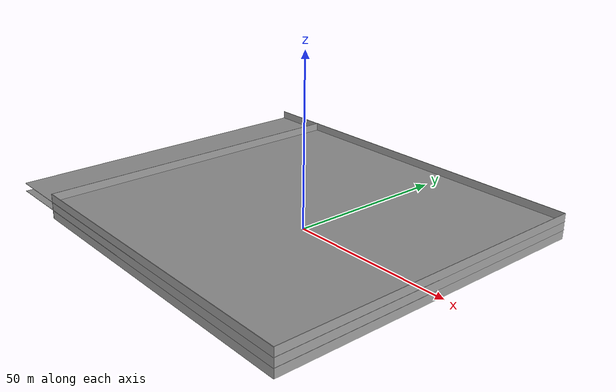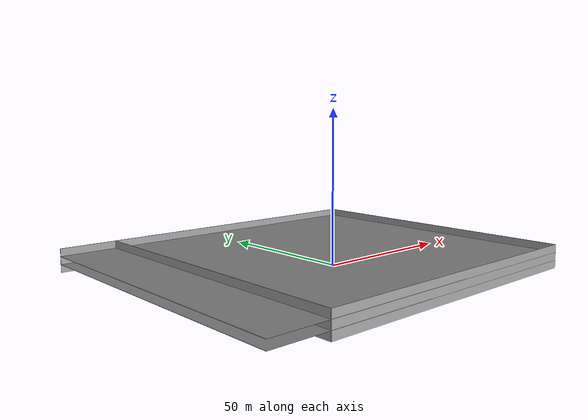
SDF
<?xml version='1.0'?>
<sdf version='1.7'>
  <model name='testx'>
    <pose>-9.53854 -0.188873 0 0 -0 0</pose>
    <link name='Door_0'>
      <collision name='Door_0_Collision'>
        <geometry>
          <box>
            <size>0.9 0.17 2</size>
          </box>
        </geometry>
        <pose>0 0 1 0 -0 0</pose>
      </collision>
      <visual name='Door_0_Visual'>
        <pose>0 0 1 0 -0 0</pose>
        <geometry>
          <box>
            <size>0.9 0.17 2</size>
          </box>
        </geometry>
        <material>
          <script>
            <uri>file://media/materials/scripts/gazebo.material</uri>
            <name>Gazebo/Grey</name>
          </script>
        </material>
      </visual>
      <pose>-25.6922 -26.6179 0 0 -0 0</pose>
    </link>
    <link name='Door_1'>
      <collision name='Door_1_Collision'>
        <geometry>
          <box>
            <size>0.9 0.17 2</size>
          </box>
        </geometry>
        <pose>0 0 1 0 -0 0</pose>
      </collision>
      <visual name='Door_1_Visual'>
        <pose>0 0 1 0 -0 0</pose>
        <geometry>
          <box>
            <size>0.9 0.17 2</size>
          </box>
        </geometry>
        <material>
          <script>
            <uri>file://media/materials/scripts/gazebo.material</uri>
            <name>Gazebo/Grey</name>
          </script>
        </material>
      </visual>
      <pose>19.8592 14.9509 0 0 -0 0</pose>
    </link>
    <link name='Door_2'>
      <collision name='Door_2_Collision'>
        <geometry>
          <box>
            <size>0.9 0.17 2</size>
          </box>
        </geometry>
        <pose>0 0 1 0 -0 0</pose>
      </collision>
      <visual name='Door_2_Visual'>
        <pose>0 0 1 0 -0 0</pose>
        <geometry>
          <box>
            <size>0.9 0.17 2</size>
          </box>
        </geometry>
        <material>
          <script>
            <uri>file://media/materials/scripts/gazebo.material</uri>
            <name>Gazebo/Grey</name>
          </script>
        </material>
      </visual>
      <pose>-26.4389 12.7106 0 0 -0 0</pose>
    </link>
    <link name='Floor_0'>
      <pose>-5e-06 1e-06 2.5 0 -0 0</pose>
      <visual name='Floor_0_Visual_0'>
        <pose>-37.9276 0 0.05 0 -0 0</pose>
        <geometry>
          <box>
            <size>40.8948 99.75 0.1</size>
          </box>
        </geometry>
        <material>
          <script>
            <uri>file://media/materials/scripts/gazebo.material</uri>
            <name>Gazebo/Grey</name>
          </script>
          <ambient>1 1 1 1</ambient>
        </material>
        <meta>
          <layer>1</layer>
        </meta>
      </visual>
      <collision name='Floor_0_Collision_0'>
        <geometry>
          <box>
            <size>40.8948 99.75 0.1</size>
          </box>
        </geometry>
        <pose>-37.9276 0 0.05 0 -0 0</pose>
      </collision>
      <visual name='Floor_0_Visual_1'>
        <pose>-16.609 -5.51796 0.05 0 -0 0</pose>
        <geometry>
          <box>
            <size>1.7424 88.7141 0.1</size>
          </box>
        </geometry>
        <material>
          <script>
            <uri>file://media/materials/scripts/gazebo.material</uri>
            <name>Gazebo/Grey</name>
          </script>
          <ambient>1 1 1 1</ambient>
        </material>
        <meta>
          <layer>1</layer>
        </meta>
      </visual>
      <collision name='Floor_0_Collision_1'>
        <geometry>
          <box>
            <size>1.7424 88.7141 0.1</size>
          </box>
        </geometry>
        <pose>-16.609 -5.51796 0.05 0 -0 0</pose>
      </collision>
      <visual name='Floor_0_Visual_2'>
        <pose>-10.1372 -10.3718 0.05 0 -0 0</pose>
        <geometry>
          <box>
            <size>11.2012 79.0064 0.1</size>
          </box>
        </geometry>
        <material>
          <script>
            <uri>file://media/materials/scripts/gazebo.material</uri>
            <name>Gazebo/Grey</name>
          </script>
          <ambient>1 1 1 1</ambient>
        </material>
        <meta>
          <layer>1</layer>
        </meta>
      </visual>
      <collision name='Floor_0_Collision_2'>
        <geometry>
          <box>
            <size>11.2012 79.0064 0.1</size>
          </box>
        </geometry>
        <pose>-10.1372 -10.3718 0.05 0 -0 0</pose>
      </collision>
      <visual name='Floor_0_Visual_3'>
        <pose>2.55744 -12.612 0.05 0 -0 0</pose>
        <geometry>
          <box>
            <size>14.1881 74.5259 0.1</size>
          </box>
        </geometry>
        <material>
          <script>
            <uri>file://media/materials/scripts/gazebo.material</uri>
            <name>Gazebo/Grey</name>
          </script>
          <ambient>1 1 1 1</ambient>
        </material>
        <meta>
          <layer>1</layer>
        </meta>
      </visual>
      <collision name='Floor_0_Collision_3'>
        <geometry>
          <box>
            <size>14.1881 74.5259 0.1</size>
          </box>
        </geometry>
        <pose>2.55744 -12.612 0.05 0 -0 0</pose>
      </collision>
      <visual name='Floor_0_Visual_4'>
        <pose>34.0133 -36.7567 0.05 0 -0 0</pose>
        <geometry>
          <box>
            <size>48.7235 26.2365 0.1</size>
          </box>
        </geometry>
        <material>
          <script>
            <uri>file://media/materials/scripts/gazebo.material</uri>
            <name>Gazebo/Grey</name>
          </script>
          <ambient>1 1 1 1</ambient>
        </material>
        <meta>
          <layer>1</layer>
        </meta>
      </visual>
      <collision name='Floor_0_Collision_4'>
        <geometry>
          <box>
            <size>48.7235 26.2365 0.1</size>
          </box>
        </geometry>
        <pose>34.0133 -36.7567 0.05 0 -0 0</pose>
      </collision>
      <visual name='Floor_0_Visual_5'>
        <pose>17.2456 13.1183 0.05 0 -0 0</pose>
        <geometry>
          <box>
            <size>13.1881 73.5135 0.1</size>
          </box>
        </geometry>
        <material>
          <script>
            <uri>file://media/materials/scripts/gazebo.material</uri>
            <name>Gazebo/Grey</name>
          </script>
          <ambient>1 1 1 1</ambient>
        </material>
        <meta>
          <layer>1</layer>
        </meta>
      </visual>
      <collision name='Floor_0_Collision_5'>
        <geometry>
          <box>
            <size>13.1881 73.5135 0.1</size>
          </box>
        </geometry>
        <pose>17.2456 13.1183 0.05 0 -0 0</pose>
      </collision>
      <visual name='Floor_0_Visual_6'>
        <pose>41.1073 8.34704 0.05 0 -0 0</pose>
        <geometry>
          <box>
            <size>34.5354 63.971 0.1</size>
          </box>
        </geometry>
        <material>
          <script>
            <uri>file://media/materials/scripts/gazebo.material</uri>
            <name>Gazebo/Grey</name>
          </script>
          <ambient>1 1 1 1</ambient>
        </material>
        <meta>
          <layer>1</layer>
        </meta>
      </visual>
      <collision name='Floor_0_Collision_6'>
        <geometry>
          <box>
            <size>34.5354 63.971 0.1</size>
          </box>
        </geometry>
        <pose>41.1073 8.34704 0.05 0 -0 0</pose>
      </collision>
      <visual name='Floor_0_Visual_7'>
        <pose>10.1515 14.8683 0.05 0 -0 0</pose>
        <geometry>
          <box>
            <size>1 70.0135 0.1</size>
          </box>
        </geometry>
        <material>
          <script>
            <uri>file://media/materials/scripts/gazebo.material</uri>
            <name>Gazebo/Grey</name>
          </script>
          <ambient>1 1 1 1</ambient>
        </material>
        <meta>
          <layer>1</layer>
        </meta>
      </visual>
      <collision name='Floor_0_Collision_7'>
        <geometry>
          <box>
            <size>1 70.0135 0.1</size>
          </box>
        </geometry>
        <pose>10.1515 14.8683 0.05 0 -0 0</pose>
      </collision>
      <visual name='Floor_0_Visual_8'>
        <pose>3.05744 37.263 0.05 0 -0 0</pose>
        <geometry>
          <box>
            <size>13.1881 25.2241 0.1</size>
          </box>
        </geometry>
        <material>
          <script>
            <uri>file://media/materials/scripts/gazebo.material</uri>
            <name>Gazebo/Grey</name>
          </script>
          <ambient>1 1 1 1</ambient>
        </material>
        <meta>
          <layer>1</layer>
        </meta>
      </visual>
      <collision name='Floor_0_Collision_8'>
        <geometry>
          <box>
            <size>13.1881 25.2241 0.1</size>
          </box>
        </geometry>
        <pose>3.05744 37.263 0.05 0 -0 0</pose>
      </collision>
      <visual name='Floor_0_Visual_9'>
        <pose>-4.03662 39.013 0.05 0 -0 0</pose>
        <geometry>
          <box>
            <size>1 21.7241 0.1</size>
          </box>
        </geometry>
        <material>
          <script>
            <uri>file://media/materials/scripts/gazebo.material</uri>
            <name>Gazebo/Grey</name>
          </script>
          <ambient>1 1 1 1</ambient>
        </material>
        <meta>
          <layer>1</layer>
        </meta>
      </visual>
      <collision name='Floor_0_Collision_9'>
        <geometry>
          <box>
            <size>1 21.7241 0.1</size>
          </box>
        </geometry>
        <pose>-4.03662 39.013 0.05 0 -0 0</pose>
      </collision>
      <visual name='Floor_0_Visual_10'>
        <pose>-9.6372 39.5032 0.05 0 -0 0</pose>
        <geometry>
          <box>
            <size>10.2012 20.7436 0.1</size>
          </box>
        </geometry>
        <material>
          <script>
            <uri>file://media/materials/scripts/gazebo.material</uri>
            <name>Gazebo/Grey</name>
          </script>
          <ambient>1 1 1 1</ambient>
        </material>
        <meta>
          <layer>1</layer>
        </meta>
      </visual>
      <collision name='Floor_0_Collision_10'>
        <geometry>
          <box>
            <size>10.2012 20.7436 0.1</size>
          </box>
        </geometry>
        <pose>-9.6372 39.5032 0.05 0 -0 0</pose>
      </collision>
      <visual name='Floor_0_Visual_11'>
        <pose>-15.2378 41.2532 0.05 0 -0 0</pose>
        <geometry>
          <box>
            <size>1 17.2436 0.1</size>
          </box>
        </geometry>
        <material>
          <script>
            <uri>file://media/materials/scripts/gazebo.material</uri>
            <name>Gazebo/Grey</name>
          </script>
          <ambient>1 1 1 1</ambient>
        </material>
        <meta>
          <layer>1</layer>
        </meta>
      </visual>
      <collision name='Floor_0_Collision_11'>
        <geometry>
          <box>
            <size>1 17.2436 0.1</size>
          </box>
        </geometry>
        <pose>-15.2378 41.2532 0.05 0 -0 0</pose>
      </collision>
      <visual name='Floor_0_Visual_12'>
        <pose>-16.109 44.357 0.05 0 -0 0</pose>
        <geometry>
          <box>
            <size>0.742401 11.0359 0.1</size>
          </box>
        </geometry>
        <material>
          <script>
            <uri>file://media/materials/scripts/gazebo.material</uri>
            <name>Gazebo/Grey</name>
          </script>
          <ambient>1 1 1 1</ambient>
        </material>
        <meta>
          <layer>1</layer>
        </meta>
      </visual>
      <collision name='Floor_0_Collision_12'>
        <geometry>
          <box>
            <size>0.742401 11.0359 0.1</size>
          </box>
        </geometry>
        <pose>-16.109 44.357 0.05 0 -0 0</pose>
      </collision>
      <visual name='Floor_0_Visual_13'>
        <pose>41.6073 45.1038 0.05 0 -0 0</pose>
        <geometry>
          <box>
            <size>33.5354 9.54244 0.1</size>
          </box>
        </geometry>
        <material>
          <script>
            <uri>file://media/materials/scripts/gazebo.material</uri>
            <name>Gazebo/Grey</name>
          </script>
          <ambient>1 1 1 1</ambient>
        </material>
        <meta>
          <layer>1</layer>
        </meta>
      </visual>
      <collision name='Floor_0_Collision_13'>
        <geometry>
          <box>
            <size>33.5354 9.54244 0.1</size>
          </box>
        </geometry>
        <pose>41.6073 45.1038 0.05 0 -0 0</pose>
      </collision>
      <visual name='Floor_0_Visual_14'>
        <pose>-16.9802 46.107 0.05 0 -0 0</pose>
        <geometry>
          <box>
            <size>1 7.53592 0.1</size>
          </box>
        </geometry>
        <material>
          <script>
            <uri>file://media/materials/scripts/gazebo.material</uri>
            <name>Gazebo/Grey</name>
          </script>
          <ambient>1 1 1 1</ambient>
        </material>
        <meta>
          <layer>1</layer>
        </meta>
      </visual>
      <collision name='Floor_0_Collision_14'>
        <geometry>
          <box>
            <size>1 7.53592 0.1</size>
          </box>
        </geometry>
        <pose>-16.9802 46.107 0.05 0 -0 0</pose>
      </collision>
      <visual name='Floor_0_Visual_15'>
        <pose>24.3396 46.8538 0.05 0 -0 0</pose>
        <geometry>
          <box>
            <size>1 6.04244 0.1</size>
          </box>
        </geometry>
        <material>
          <script>
            <uri>file://media/materials/scripts/gazebo.material</uri>
            <name>Gazebo/Grey</name>
          </script>
          <ambient>1 1 1 1</ambient>
        </material>
        <meta>
          <layer>1</layer>
        </meta>
      </visual>
      <collision name='Floor_0_Collision_15'>
        <geometry>
          <box>
            <size>1 6.04244 0.1</size>
          </box>
        </geometry>
        <pose>24.3396 46.8538 0.05 0 -0 0</pose>
      </collision>
    </link>
    <link name='Floor_1'>
      <collision name='Floor_1_Collision'>
        <geometry>
          <box>
            <size>116.75 99.75 0.1</size>
          </box>
        </geometry>
        <pose>0 0 0.05 0 -0 0</pose>
      </collision>
      <visual name='Floor_1_Visual'>
        <pose>0 0 0.05 0 -0 0</pose>
        <geometry>
          <box>
            <size>116.75 99.75 0.1</size>
          </box>
        </geometry>
        <material>
          <script>
            <uri>file://media/materials/scripts/gazebo.material</uri>
            <name>Gazebo/Grey</name>
          </script>
          <ambient>1 1 1 1</ambient>
        </material>
        <meta>
          <layer>2</layer>
        </meta>
      </visual>
      <pose>-5e-06 1e-06 5 0 -0 0</pose>
    </link>
    <link name='Stairs_0'>
      <visual name='Stairs_0_Visual_0'>
        <pose>-15.2378 32.5147 0.083333 0 -0 0</pose>
        <geometry>
          <box>
            <size>1 0.233333 0.166667</size>
          </box>
        </geometry>
        <material>
          <script>
            <uri>file://media/materials/scripts/gazebo.material</uri>
            <name>Gazebo/Grey</name>
          </script>
          <ambient>1 1 1 1</ambient>
        </material>
        <meta>
          <layer>0</layer>
        </meta>
      </visual>
      <collision name='Stairs_0_Collision_0'>
        <geometry>
          <box>
            <size>1 0.233333 0.166667</size>
          </box>
        </geometry>
        <pose>-15.2378 32.5147 0.083333 0 -0 0</pose>
      </collision>
      <visual name='Stairs_0_Visual_1'>
        <pose>-15.2378 32.2814 0.25 0 -0 0</pose>
        <geometry>
          <box>
            <size>1 0.233333 0.166667</size>
          </box>
        </geometry>
        <material>
          <script>
            <uri>file://media/materials/scripts/gazebo.material</uri>
            <name>Gazebo/Grey</name>
          </script>
          <ambient>1 1 1 1</ambient>
        </material>
        <meta>
          <layer>0</layer>
        </meta>
      </visual>
      <collision name='Stairs_0_Collision_1'>
        <geometry>
          <box>
            <size>1 0.233333 0.166667</size>
          </box>
        </geometry>
        <pose>-15.2378 32.2814 0.25 0 -0 0</pose>
      </collision>
      <visual name='Stairs_0_Visual_2'>
        <pose>-15.2378 32.0481 0.416667 0 -0 0</pose>
        <geometry>
          <box>
            <size>1 0.233333 0.166667</size>
          </box>
        </geometry>
        <material>
          <script>
            <uri>file://media/materials/scripts/gazebo.material</uri>
            <name>Gazebo/Grey</name>
          </script>
          <ambient>1 1 1 1</ambient>
        </material>
        <meta>
          <layer>0</layer>
        </meta>
      </visual>
      <collision name='Stairs_0_Collision_2'>
        <geometry>
          <box>
            <size>1 0.233333 0.166667</size>
          </box>
        </geometry>
        <pose>-15.2378 32.0481 0.416667 0 -0 0</pose>
      </collision>
      <visual name='Stairs_0_Visual_3'>
        <pose>-15.2378 31.8147 0.583333 0 -0 0</pose>
        <geometry>
          <box>
            <size>1 0.233333 0.166667</size>
          </box>
        </geometry>
        <material>
          <script>
            <uri>file://media/materials/scripts/gazebo.material</uri>
            <name>Gazebo/Grey</name>
          </script>
          <ambient>1 1 1 1</ambient>
        </material>
        <meta>
          <layer>0</layer>
        </meta>
      </visual>
      <collision name='Stairs_0_Collision_3'>
        <geometry>
          <box>
            <size>1 0.233333 0.166667</size>
          </box>
        </geometry>
        <pose>-15.2378 31.8147 0.583333 0 -0 0</pose>
      </collision>
      <visual name='Stairs_0_Visual_4'>
        <pose>-15.2378 31.5814 0.75 0 -0 0</pose>
        <geometry>
          <box>
            <size>1 0.233333 0.166667</size>
          </box>
        </geometry>
        <material>
          <script>
            <uri>file://media/materials/scripts/gazebo.material</uri>
            <name>Gazebo/Grey</name>
          </script>
          <ambient>1 1 1 1</ambient>
        </material>
        <meta>
          <layer>0</layer>
        </meta>
      </visual>
      <collision name='Stairs_0_Collision_4'>
        <geometry>
          <box>
            <size>1 0.233333 0.166667</size>
          </box>
        </geometry>
        <pose>-15.2378 31.5814 0.75 0 -0 0</pose>
      </collision>
      <visual name='Stairs_0_Visual_5'>
        <pose>-15.2378 31.3481 0.916667 0 -0 0</pose>
        <geometry>
          <box>
            <size>1 0.233333 0.166667</size>
          </box>
        </geometry>
        <material>
          <script>
            <uri>file://media/materials/scripts/gazebo.material</uri>
            <name>Gazebo/Grey</name>
          </script>
          <ambient>1 1 1 1</ambient>
        </material>
        <meta>
          <layer>0</layer>
        </meta>
      </visual>
      <collision name='Stairs_0_Collision_5'>
        <geometry>
          <box>
            <size>1 0.233333 0.166667</size>
          </box>
        </geometry>
        <pose>-15.2378 31.3481 0.916667 0 -0 0</pose>
      </collision>
      <visual name='Stairs_0_Visual_6'>
        <pose>-15.2378 31.1147 1.08333 0 -0 0</pose>
        <geometry>
          <box>
            <size>1 0.233333 0.166667</size>
          </box>
        </geometry>
        <material>
          <script>
            <uri>file://media/materials/scripts/gazebo.material</uri>
            <name>Gazebo/Grey</name>
          </script>
          <ambient>1 1 1 1</ambient>
        </material>
        <meta>
          <layer>0</layer>
        </meta>
      </visual>
      <collision name='Stairs_0_Collision_6'>
        <geometry>
          <box>
            <size>1 0.233333 0.166667</size>
          </box>
        </geometry>
        <pose>-15.2378 31.1147 1.08333 0 -0 0</pose>
      </collision>
      <visual name='Stairs_0_Visual_7'>
        <pose>-15.2378 30.8814 1.25 0 -0 0</pose>
        <geometry>
          <box>
            <size>1 0.233333 0.166667</size>
          </box>
        </geometry>
        <material>
          <script>
            <uri>file://media/materials/scripts/gazebo.material</uri>
            <name>Gazebo/Grey</name>
          </script>
          <ambient>1 1 1 1</ambient>
        </material>
        <meta>
          <layer>0</layer>
        </meta>
      </visual>
      <collision name='Stairs_0_Collision_7'>
        <geometry>
          <box>
            <size>1 0.233333 0.166667</size>
          </box>
        </geometry>
        <pose>-15.2378 30.8814 1.25 0 -0 0</pose>
      </collision>
      <visual name='Stairs_0_Visual_8'>
        <pose>-15.2378 30.6481 1.41667 0 -0 0</pose>
        <geometry>
          <box>
            <size>1 0.233333 0.166667</size>
          </box>
        </geometry>
        <material>
          <script>
            <uri>file://media/materials/scripts/gazebo.material</uri>
            <name>Gazebo/Grey</name>
          </script>
          <ambient>1 1 1 1</ambient>
        </material>
        <meta>
          <layer>0</layer>
        </meta>
      </visual>
      <collision name='Stairs_0_Collision_8'>
        <geometry>
          <box>
            <size>1 0.233333 0.166667</size>
          </box>
        </geometry>
        <pose>-15.2378 30.6481 1.41667 0 -0 0</pose>
      </collision>
      <visual name='Stairs_0_Visual_9'>
        <pose>-15.2378 30.4147 1.58333 0 -0 0</pose>
        <geometry>
          <box>
            <size>1 0.233333 0.166667</size>
          </box>
        </geometry>
        <material>
          <script>
            <uri>file://media/materials/scripts/gazebo.material</uri>
            <name>Gazebo/Grey</name>
          </script>
          <ambient>1 1 1 1</ambient>
        </material>
        <meta>
          <layer>0</layer>
        </meta>
      </visual>
      <collision name='Stairs_0_Collision_9'>
        <geometry>
          <box>
            <size>1 0.233333 0.166667</size>
          </box>
        </geometry>
        <pose>-15.2378 30.4147 1.58333 0 -0 0</pose>
      </collision>
      <visual name='Stairs_0_Visual_10'>
        <pose>-15.2378 30.1814 1.75 0 -0 0</pose>
        <geometry>
          <box>
            <size>1 0.233333 0.166667</size>
          </box>
        </geometry>
        <material>
          <script>
            <uri>file://media/materials/scripts/gazebo.material</uri>
            <name>Gazebo/Grey</name>
          </script>
          <ambient>1 1 1 1</ambient>
        </material>
        <meta>
          <layer>0</layer>
        </meta>
      </visual>
      <collision name='Stairs_0_Collision_10'>
        <geometry>
          <box>
            <size>1 0.233333 0.166667</size>
          </box>
        </geometry>
        <pose>-15.2378 30.1814 1.75 0 -0 0</pose>
      </collision>
      <visual name='Stairs_0_Visual_11'>
        <pose>-15.2378 29.9481 1.91667 0 -0 0</pose>
        <geometry>
          <box>
            <size>1 0.233333 0.166667</size>
          </box>
        </geometry>
        <material>
          <script>
            <uri>file://media/materials/scripts/gazebo.material</uri>
            <name>Gazebo/Grey</name>
          </script>
          <ambient>1 1 1 1</ambient>
        </material>
        <meta>
          <layer>0</layer>
        </meta>
      </visual>
      <collision name='Stairs_0_Collision_11'>
        <geometry>
          <box>
            <size>1 0.233333 0.166667</size>
          </box>
        </geometry>
        <pose>-15.2378 29.9481 1.91667 0 -0 0</pose>
      </collision>
      <visual name='Stairs_0_Visual_12'>
        <pose>-15.2378 29.7147 2.08333 0 -0 0</pose>
        <geometry>
          <box>
            <size>1 0.233333 0.166667</size>
          </box>
        </geometry>
        <material>
          <script>
            <uri>file://media/materials/scripts/gazebo.material</uri>
            <name>Gazebo/Grey</name>
          </script>
          <ambient>1 1 1 1</ambient>
        </material>
        <meta>
          <layer>0</layer>
        </meta>
      </visual>
      <collision name='Stairs_0_Collision_12'>
        <geometry>
          <box>
            <size>1 0.233333 0.166667</size>
          </box>
        </geometry>
        <pose>-15.2378 29.7147 2.08333 0 -0 0</pose>
      </collision>
      <visual name='Stairs_0_Visual_13'>
        <pose>-15.2378 29.4814 2.25 0 -0 0</pose>
        <geometry>
          <box>
            <size>1 0.233333 0.166667</size>
          </box>
        </geometry>
        <material>
          <script>
            <uri>file://media/materials/scripts/gazebo.material</uri>
            <name>Gazebo/Grey</name>
          </script>
          <ambient>1 1 1 1</ambient>
        </material>
        <meta>
          <layer>0</layer>
        </meta>
      </visual>
      <collision name='Stairs_0_Collision_13'>
        <geometry>
          <box>
            <size>1 0.233333 0.166667</size>
          </box>
        </geometry>
        <pose>-15.2378 29.4814 2.25 0 -0 0</pose>
      </collision>
      <visual name='Stairs_0_Visual_14'>
        <pose>-15.2378 29.2481 2.41667 0 -0 0</pose>
        <geometry>
          <box>
            <size>1 0.233333 0.166667</size>
          </box>
        </geometry>
        <material>
          <script>
            <uri>file://media/materials/scripts/gazebo.material</uri>
            <name>Gazebo/Grey</name>
          </script>
          <ambient>1 1 1 1</ambient>
        </material>
        <meta>
          <layer>0</layer>
        </meta>
      </visual>
      <collision name='Stairs_0_Collision_14'>
        <geometry>
          <box>
            <size>1 0.233333 0.166667</size>
          </box>
        </geometry>
        <pose>-15.2378 29.2481 2.41667 0 -0 0</pose>
      </collision>
    </link>
    <link name='Stairs_1'>
      <visual name='Stairs_1_Visual_0'>
        <pose>10.1515 -20.2551 0.083333 0 -0 0</pose>
        <geometry>
          <box>
            <size>1 0.233333 0.166667</size>
          </box>
        </geometry>
        <material>
          <script>
            <uri>file://media/materials/scripts/gazebo.material</uri>
            <name>Gazebo/Grey</name>
          </script>
          <ambient>1 1 1 1</ambient>
        </material>
        <meta>
          <layer>0</layer>
        </meta>
      </visual>
      <collision name='Stairs_1_Collision_0'>
        <geometry>
          <box>
            <size>1 0.233333 0.166667</size>
          </box>
        </geometry>
        <pose>10.1515 -20.2551 0.083333 0 -0 0</pose>
      </collision>
      <visual name='Stairs_1_Visual_1'>
        <pose>10.1515 -20.4885 0.25 0 -0 0</pose>
        <geometry>
          <box>
            <size>1 0.233333 0.166667</size>
          </box>
        </geometry>
        <material>
          <script>
            <uri>file://media/materials/scripts/gazebo.material</uri>
            <name>Gazebo/Grey</name>
          </script>
          <ambient>1 1 1 1</ambient>
        </material>
        <meta>
          <layer>0</layer>
        </meta>
      </visual>
      <collision name='Stairs_1_Collision_1'>
        <geometry>
          <box>
            <size>1 0.233333 0.166667</size>
          </box>
        </geometry>
        <pose>10.1515 -20.4885 0.25 0 -0 0</pose>
      </collision>
      <visual name='Stairs_1_Visual_2'>
        <pose>10.1515 -20.7218 0.416667 0 -0 0</pose>
        <geometry>
          <box>
            <size>1 0.233333 0.166667</size>
          </box>
        </geometry>
        <material>
          <script>
            <uri>file://media/materials/scripts/gazebo.material</uri>
            <name>Gazebo/Grey</name>
          </script>
          <ambient>1 1 1 1</ambient>
        </material>
        <meta>
          <layer>0</layer>
        </meta>
      </visual>
      <collision name='Stairs_1_Collision_2'>
        <geometry>
          <box>
            <size>1 0.233333 0.166667</size>
          </box>
        </geometry>
        <pose>10.1515 -20.7218 0.416667 0 -0 0</pose>
      </collision>
      <visual name='Stairs_1_Visual_3'>
        <pose>10.1515 -20.9551 0.583333 0 -0 0</pose>
        <geometry>
          <box>
            <size>1 0.233333 0.166667</size>
          </box>
        </geometry>
        <material>
          <script>
            <uri>file://media/materials/scripts/gazebo.material</uri>
            <name>Gazebo/Grey</name>
          </script>
          <ambient>1 1 1 1</ambient>
        </material>
        <meta>
          <layer>0</layer>
        </meta>
      </visual>
      <collision name='Stairs_1_Collision_3'>
        <geometry>
          <box>
            <size>1 0.233333 0.166667</size>
          </box>
        </geometry>
        <pose>10.1515 -20.9551 0.583333 0 -0 0</pose>
      </collision>
      <visual name='Stairs_1_Visual_4'>
        <pose>10.1515 -21.1885 0.75 0 -0 0</pose>
        <geometry>
          <box>
            <size>1 0.233333 0.166667</size>
          </box>
        </geometry>
        <material>
          <script>
            <uri>file://media/materials/scripts/gazebo.material</uri>
            <name>Gazebo/Grey</name>
          </script>
          <ambient>1 1 1 1</ambient>
        </material>
        <meta>
          <layer>0</layer>
        </meta>
      </visual>
      <collision name='Stairs_1_Collision_4'>
        <geometry>
          <box>
            <size>1 0.233333 0.166667</size>
          </box>
        </geometry>
        <pose>10.1515 -21.1885 0.75 0 -0 0</pose>
      </collision>
      <visual name='Stairs_1_Visual_5'>
        <pose>10.1515 -21.4218 0.916667 0 -0 0</pose>
        <geometry>
          <box>
            <size>1 0.233333 0.166667</size>
          </box>
        </geometry>
        <material>
          <script>
            <uri>file://media/materials/scripts/gazebo.material</uri>
            <name>Gazebo/Grey</name>
          </script>
          <ambient>1 1 1 1</ambient>
        </material>
        <meta>
          <layer>0</layer>
        </meta>
      </visual>
      <collision name='Stairs_1_Collision_5'>
        <geometry>
          <box>
            <size>1 0.233333 0.166667</size>
          </box>
        </geometry>
        <pose>10.1515 -21.4218 0.916667 0 -0 0</pose>
      </collision>
      <visual name='Stairs_1_Visual_6'>
        <pose>10.1515 -21.6551 1.08333 0 -0 0</pose>
        <geometry>
          <box>
            <size>1 0.233333 0.166667</size>
          </box>
        </geometry>
        <material>
          <script>
            <uri>file://media/materials/scripts/gazebo.material</uri>
            <name>Gazebo/Grey</name>
          </script>
          <ambient>1 1 1 1</ambient>
        </material>
        <meta>
          <layer>0</layer>
        </meta>
      </visual>
      <collision name='Stairs_1_Collision_6'>
        <geometry>
          <box>
            <size>1 0.233333 0.166667</size>
          </box>
        </geometry>
        <pose>10.1515 -21.6551 1.08333 0 -0 0</pose>
      </collision>
      <visual name='Stairs_1_Visual_7'>
        <pose>10.1515 -21.8885 1.25 0 -0 0</pose>
        <geometry>
          <box>
            <size>1 0.233333 0.166667</size>
          </box>
        </geometry>
        <material>
          <script>
            <uri>file://media/materials/scripts/gazebo.material</uri>
            <name>Gazebo/Grey</name>
          </script>
          <ambient>1 1 1 1</ambient>
        </material>
        <meta>
          <layer>0</layer>
        </meta>
      </visual>
      <collision name='Stairs_1_Collision_7'>
        <geometry>
          <box>
            <size>1 0.233333 0.166667</size>
          </box>
        </geometry>
        <pose>10.1515 -21.8885 1.25 0 -0 0</pose>
      </collision>
      <visual name='Stairs_1_Visual_8'>
        <pose>10.1515 -22.1218 1.41667 0 -0 0</pose>
        <geometry>
          <box>
            <size>1 0.233333 0.166667</size>
          </box>
        </geometry>
        <material>
          <script>
            <uri>file://media/materials/scripts/gazebo.material</uri>
            <name>Gazebo/Grey</name>
          </script>
          <ambient>1 1 1 1</ambient>
        </material>
        <meta>
          <layer>0</layer>
        </meta>
      </visual>
      <collision name='Stairs_1_Collision_8'>
        <geometry>
          <box>
            <size>1 0.233333 0.166667</size>
          </box>
        </geometry>
        <pose>10.1515 -22.1218 1.41667 0 -0 0</pose>
      </collision>
      <visual name='Stairs_1_Visual_9'>
        <pose>10.1515 -22.3551 1.58333 0 -0 0</pose>
        <geometry>
          <box>
            <size>1 0.233333 0.166667</size>
          </box>
        </geometry>
        <material>
          <script>
            <uri>file://media/materials/scripts/gazebo.material</uri>
            <name>Gazebo/Grey</name>
          </script>
          <ambient>1 1 1 1</ambient>
        </material>
        <meta>
          <layer>0</layer>
        </meta>
      </visual>
      <collision name='Stairs_1_Collision_9'>
        <geometry>
          <box>
            <size>1 0.233333 0.166667</size>
          </box>
        </geometry>
        <pose>10.1515 -22.3551 1.58333 0 -0 0</pose>
      </collision>
      <visual name='Stairs_1_Visual_10'>
        <pose>10.1515 -22.5885 1.75 0 -0 0</pose>
        <geometry>
          <box>
            <size>1 0.233333 0.166667</size>
          </box>
        </geometry>
        <material>
          <script>
            <uri>file://media/materials/scripts/gazebo.material</uri>
            <name>Gazebo/Grey</name>
          </script>
          <ambient>1 1 1 1</ambient>
        </material>
        <meta>
          <layer>0</layer>
        </meta>
      </visual>
      <collision name='Stairs_1_Collision_10'>
        <geometry>
          <box>
            <size>1 0.233333 0.166667</size>
          </box>
        </geometry>
        <pose>10.1515 -22.5885 1.75 0 -0 0</pose>
      </collision>
      <visual name='Stairs_1_Visual_11'>
        <pose>10.1515 -22.8218 1.91667 0 -0 0</pose>
        <geometry>
          <box>
            <size>1 0.233333 0.166667</size>
          </box>
        </geometry>
        <material>
          <script>
            <uri>file://media/materials/scripts/gazebo.material</uri>
            <name>Gazebo/Grey</name>
          </script>
          <ambient>1 1 1 1</ambient>
        </material>
        <meta>
          <layer>0</layer>
        </meta>
      </visual>
      <collision name='Stairs_1_Collision_11'>
        <geometry>
          <box>
            <size>1 0.233333 0.166667</size>
          </box>
        </geometry>
        <pose>10.1515 -22.8218 1.91667 0 -0 0</pose>
      </collision>
      <visual name='Stairs_1_Visual_12'>
        <pose>10.1515 -23.0551 2.08333 0 -0 0</pose>
        <geometry>
          <box>
            <size>1 0.233333 0.166667</size>
          </box>
        </geometry>
        <material>
          <script>
            <uri>file://media/materials/scripts/gazebo.material</uri>
            <name>Gazebo/Grey</name>
          </script>
          <ambient>1 1 1 1</ambient>
        </material>
        <meta>
          <layer>0</layer>
        </meta>
      </visual>
      <collision name='Stairs_1_Collision_12'>
        <geometry>
          <box>
            <size>1 0.233333 0.166667</size>
          </box>
        </geometry>
        <pose>10.1515 -23.0551 2.08333 0 -0 0</pose>
      </collision>
      <visual name='Stairs_1_Visual_13'>
        <pose>10.1515 -23.2885 2.25 0 -0 0</pose>
        <geometry>
          <box>
            <size>1 0.233333 0.166667</size>
          </box>
        </geometry>
        <material>
          <script>
            <uri>file://media/materials/scripts/gazebo.material</uri>
            <name>Gazebo/Grey</name>
          </script>
          <ambient>1 1 1 1</ambient>
        </material>
        <meta>
          <layer>0</layer>
        </meta>
      </visual>
      <collision name='Stairs_1_Collision_13'>
        <geometry>
          <box>
            <size>1 0.233333 0.166667</size>
          </box>
        </geometry>
        <pose>10.1515 -23.2885 2.25 0 -0 0</pose>
      </collision>
      <visual name='Stairs_1_Visual_14'>
        <pose>10.1515 -23.5218 2.41667 0 -0 0</pose>
        <geometry>
          <box>
            <size>1 0.233333 0.166667</size>
          </box>
        </geometry>
        <material>
          <script>
            <uri>file://media/materials/scripts/gazebo.material</uri>
            <name>Gazebo/Grey</name>
          </script>
          <ambient>1 1 1 1</ambient>
        </material>
        <meta>
          <layer>0</layer>
        </meta>
      </visual>
      <collision name='Stairs_1_Collision_14'>
        <geometry>
          <box>
            <size>1 0.233333 0.166667</size>
          </box>
        </geometry>
        <pose>10.1515 -23.5218 2.41667 0 -0 0</pose>
      </collision>
    </link>
    <link name='Stairs_2'>
      <visual name='Stairs_2_Visual_0'>
        <pose>-4.03663 28.0343 0.083333 0 -0 0</pose>
        <geometry>
          <box>
            <size>1 0.233333 0.166667</size>
          </box>
        </geometry>
        <material>
          <script>
            <uri>file://media/materials/scripts/gazebo.material</uri>
            <name>Gazebo/Grey</name>
          </script>
          <ambient>1 1 1 1</ambient>
        </material>
        <meta>
          <layer>0</layer>
        </meta>
      </visual>
      <collision name='Stairs_2_Collision_0'>
        <geometry>
          <box>
            <size>1 0.233333 0.166667</size>
          </box>
        </geometry>
        <pose>-4.03663 28.0343 0.083333 0 -0 0</pose>
      </collision>
      <visual name='Stairs_2_Visual_1'>
        <pose>-4.03663 27.8009 0.25 0 -0 0</pose>
        <geometry>
          <box>
            <size>1 0.233333 0.166667</size>
          </box>
        </geometry>
        <material>
          <script>
            <uri>file://media/materials/scripts/gazebo.material</uri>
            <name>Gazebo/Grey</name>
          </script>
          <ambient>1 1 1 1</ambient>
        </material>
        <meta>
          <layer>0</layer>
        </meta>
      </visual>
      <collision name='Stairs_2_Collision_1'>
        <geometry>
          <box>
            <size>1 0.233333 0.166667</size>
          </box>
        </geometry>
        <pose>-4.03663 27.8009 0.25 0 -0 0</pose>
      </collision>
      <visual name='Stairs_2_Visual_2'>
        <pose>-4.03663 27.5676 0.416667 0 -0 0</pose>
        <geometry>
          <box>
            <size>1 0.233333 0.166667</size>
          </box>
        </geometry>
        <material>
          <script>
            <uri>file://media/materials/scripts/gazebo.material</uri>
            <name>Gazebo/Grey</name>
          </script>
          <ambient>1 1 1 1</ambient>
        </material>
        <meta>
          <layer>0</layer>
        </meta>
      </visual>
      <collision name='Stairs_2_Collision_2'>
        <geometry>
          <box>
            <size>1 0.233333 0.166667</size>
          </box>
        </geometry>
        <pose>-4.03663 27.5676 0.416667 0 -0 0</pose>
      </collision>
      <visual name='Stairs_2_Visual_3'>
        <pose>-4.03663 27.3343 0.583333 0 -0 0</pose>
        <geometry>
          <box>
            <size>1 0.233333 0.166667</size>
          </box>
        </geometry>
        <material>
          <script>
            <uri>file://media/materials/scripts/gazebo.material</uri>
            <name>Gazebo/Grey</name>
          </script>
          <ambient>1 1 1 1</ambient>
        </material>
        <meta>
          <layer>0</layer>
        </meta>
      </visual>
      <collision name='Stairs_2_Collision_3'>
        <geometry>
          <box>
            <size>1 0.233333 0.166667</size>
          </box>
        </geometry>
        <pose>-4.03663 27.3343 0.583333 0 -0 0</pose>
      </collision>
      <visual name='Stairs_2_Visual_4'>
        <pose>-4.03663 27.1009 0.75 0 -0 0</pose>
        <geometry>
          <box>
            <size>1 0.233333 0.166667</size>
          </box>
        </geometry>
        <material>
          <script>
            <uri>file://media/materials/scripts/gazebo.material</uri>
            <name>Gazebo/Grey</name>
          </script>
          <ambient>1 1 1 1</ambient>
        </material>
        <meta>
          <layer>0</layer>
        </meta>
      </visual>
      <collision name='Stairs_2_Collision_4'>
        <geometry>
          <box>
            <size>1 0.233333 0.166667</size>
          </box>
        </geometry>
        <pose>-4.03663 27.1009 0.75 0 -0 0</pose>
      </collision>
      <visual name='Stairs_2_Visual_5'>
        <pose>-4.03663 26.8676 0.916667 0 -0 0</pose>
        <geometry>
          <box>
            <size>1 0.233333 0.166667</size>
          </box>
        </geometry>
        <material>
          <script>
            <uri>file://media/materials/scripts/gazebo.material</uri>
            <name>Gazebo/Grey</name>
          </script>
          <ambient>1 1 1 1</ambient>
        </material>
        <meta>
          <layer>0</layer>
        </meta>
      </visual>
      <collision name='Stairs_2_Collision_5'>
        <geometry>
          <box>
            <size>1 0.233333 0.166667</size>
          </box>
        </geometry>
        <pose>-4.03663 26.8676 0.916667 0 -0 0</pose>
      </collision>
      <visual name='Stairs_2_Visual_6'>
        <pose>-4.03663 26.6343 1.08333 0 -0 0</pose>
        <geometry>
          <box>
            <size>1 0.233333 0.166667</size>
          </box>
        </geometry>
        <material>
          <script>
            <uri>file://media/materials/scripts/gazebo.material</uri>
            <name>Gazebo/Grey</name>
          </script>
          <ambient>1 1 1 1</ambient>
        </material>
        <meta>
          <layer>0</layer>
        </meta>
      </visual>
      <collision name='Stairs_2_Collision_6'>
        <geometry>
          <box>
            <size>1 0.233333 0.166667</size>
          </box>
        </geometry>
        <pose>-4.03663 26.6343 1.08333 0 -0 0</pose>
      </collision>
      <visual name='Stairs_2_Visual_7'>
        <pose>-4.03663 26.4009 1.25 0 -0 0</pose>
        <geometry>
          <box>
            <size>1 0.233333 0.166667</size>
          </box>
        </geometry>
        <material>
          <script>
            <uri>file://media/materials/scripts/gazebo.material</uri>
            <name>Gazebo/Grey</name>
          </script>
          <ambient>1 1 1 1</ambient>
        </material>
        <meta>
          <layer>0</layer>
        </meta>
      </visual>
      <collision name='Stairs_2_Collision_7'>
        <geometry>
          <box>
            <size>1 0.233333 0.166667</size>
          </box>
        </geometry>
        <pose>-4.03663 26.4009 1.25 0 -0 0</pose>
      </collision>
      <visual name='Stairs_2_Visual_8'>
        <pose>-4.03663 26.1676 1.41667 0 -0 0</pose>
        <geometry>
          <box>
            <size>1 0.233333 0.166667</size>
          </box>
        </geometry>
        <material>
          <script>
            <uri>file://media/materials/scripts/gazebo.material</uri>
            <name>Gazebo/Grey</name>
          </script>
          <ambient>1 1 1 1</ambient>
        </material>
        <meta>
          <layer>0</layer>
        </meta>
      </visual>
      <collision name='Stairs_2_Collision_8'>
        <geometry>
          <box>
            <size>1 0.233333 0.166667</size>
          </box>
        </geometry>
        <pose>-4.03663 26.1676 1.41667 0 -0 0</pose>
      </collision>
      <visual name='Stairs_2_Visual_9'>
        <pose>-4.03663 25.9343 1.58333 0 -0 0</pose>
        <geometry>
          <box>
            <size>1 0.233333 0.166667</size>
          </box>
        </geometry>
        <material>
          <script>
            <uri>file://media/materials/scripts/gazebo.material</uri>
            <name>Gazebo/Grey</name>
          </script>
          <ambient>1 1 1 1</ambient>
        </material>
        <meta>
          <layer>0</layer>
        </meta>
      </visual>
      <collision name='Stairs_2_Collision_9'>
        <geometry>
          <box>
            <size>1 0.233333 0.166667</size>
          </box>
        </geometry>
        <pose>-4.03663 25.9343 1.58333 0 -0 0</pose>
      </collision>
      <visual name='Stairs_2_Visual_10'>
        <pose>-4.03663 25.7009 1.75 0 -0 0</pose>
        <geometry>
          <box>
            <size>1 0.233333 0.166667</size>
          </box>
        </geometry>
        <material>
          <script>
            <uri>file://media/materials/scripts/gazebo.material</uri>
            <name>Gazebo/Grey</name>
          </script>
          <ambient>1 1 1 1</ambient>
        </material>
        <meta>
          <layer>0</layer>
        </meta>
      </visual>
      <collision name='Stairs_2_Collision_10'>
        <geometry>
          <box>
            <size>1 0.233333 0.166667</size>
          </box>
        </geometry>
        <pose>-4.03663 25.7009 1.75 0 -0 0</pose>
      </collision>
      <visual name='Stairs_2_Visual_11'>
        <pose>-4.03663 25.4676 1.91667 0 -0 0</pose>
        <geometry>
          <box>
            <size>1 0.233333 0.166667</size>
          </box>
        </geometry>
        <material>
          <script>
            <uri>file://media/materials/scripts/gazebo.material</uri>
            <name>Gazebo/Grey</name>
          </script>
          <ambient>1 1 1 1</ambient>
        </material>
        <meta>
          <layer>0</layer>
        </meta>
      </visual>
      <collision name='Stairs_2_Collision_11'>
        <geometry>
          <box>
            <size>1 0.233333 0.166667</size>
          </box>
        </geometry>
        <pose>-4.03663 25.4676 1.91667 0 -0 0</pose>
      </collision>
      <visual name='Stairs_2_Visual_12'>
        <pose>-4.03663 25.2343 2.08333 0 -0 0</pose>
        <geometry>
          <box>
            <size>1 0.233333 0.166667</size>
          </box>
        </geometry>
        <material>
          <script>
            <uri>file://media/materials/scripts/gazebo.material</uri>
            <name>Gazebo/Grey</name>
          </script>
          <ambient>1 1 1 1</ambient>
        </material>
        <meta>
          <layer>0</layer>
        </meta>
      </visual>
      <collision name='Stairs_2_Collision_12'>
        <geometry>
          <box>
            <size>1 0.233333 0.166667</size>
          </box>
        </geometry>
        <pose>-4.03663 25.2343 2.08333 0 -0 0</pose>
      </collision>
      <visual name='Stairs_2_Visual_13'>
        <pose>-4.03663 25.0009 2.25 0 -0 0</pose>
        <geometry>
          <box>
            <size>1 0.233333 0.166667</size>
          </box>
        </geometry>
        <material>
          <script>
            <uri>file://media/materials/scripts/gazebo.material</uri>
            <name>Gazebo/Grey</name>
          </script>
          <ambient>1 1 1 1</ambient>
        </material>
        <meta>
          <layer>0</layer>
        </meta>
      </visual>
      <collision name='Stairs_2_Collision_13'>
        <geometry>
          <box>
            <size>1 0.233333 0.166667</size>
          </box>
        </geometry>
        <pose>-4.03663 25.0009 2.25 0 -0 0</pose>
      </collision>
      <visual name='Stairs_2_Visual_14'>
        <pose>-4.03663 24.7676 2.41667 0 -0 0</pose>
        <geometry>
          <box>
            <size>1 0.233333 0.166667</size>
          </box>
        </geometry>
        <material>
          <script>
            <uri>file://media/materials/scripts/gazebo.material</uri>
            <name>Gazebo/Grey</name>
          </script>
          <ambient>1 1 1 1</ambient>
        </material>
        <meta>
          <layer>0</layer>
        </meta>
      </visual>
      <collision name='Stairs_2_Collision_14'>
        <geometry>
          <box>
            <size>1 0.233333 0.166667</size>
          </box>
        </geometry>
        <pose>-4.03663 24.7676 2.41667 0 -0 0</pose>
      </collision>
    </link>
    <link name='Stairs_3'>
      <visual name='Stairs_3_Visual_0'>
        <pose>-16.9802 42.2224 0.083333 0 -0 0</pose>
        <geometry>
          <box>
            <size>1 0.233333 0.166667</size>
          </box>
        </geometry>
        <material>
          <script>
            <uri>file://media/materials/scripts/gazebo.material</uri>
            <name>Gazebo/Grey</name>
          </script>
          <ambient>1 1 1 1</ambient>
        </material>
        <meta>
          <layer>0</layer>
        </meta>
      </visual>
      <collision name='Stairs_3_Collision_0'>
        <geometry>
          <box>
            <size>1 0.233333 0.166667</size>
          </box>
        </geometry>
        <pose>-16.9802 42.2224 0.083333 0 -0 0</pose>
      </collision>
      <visual name='Stairs_3_Visual_1'>
        <pose>-16.9802 41.9891 0.25 0 -0 0</pose>
        <geometry>
          <box>
            <size>1 0.233333 0.166667</size>
          </box>
        </geometry>
        <material>
          <script>
            <uri>file://media/materials/scripts/gazebo.material</uri>
            <name>Gazebo/Grey</name>
          </script>
          <ambient>1 1 1 1</ambient>
        </material>
        <meta>
          <layer>0</layer>
        </meta>
      </visual>
      <collision name='Stairs_3_Collision_1'>
        <geometry>
          <box>
            <size>1 0.233333 0.166667</size>
          </box>
        </geometry>
        <pose>-16.9802 41.9891 0.25 0 -0 0</pose>
      </collision>
      <visual name='Stairs_3_Visual_2'>
        <pose>-16.9802 41.7557 0.416667 0 -0 0</pose>
        <geometry>
          <box>
            <size>1 0.233333 0.166667</size>
          </box>
        </geometry>
        <material>
          <script>
            <uri>file://media/materials/scripts/gazebo.material</uri>
            <name>Gazebo/Grey</name>
          </script>
          <ambient>1 1 1 1</ambient>
        </material>
        <meta>
          <layer>0</layer>
        </meta>
      </visual>
      <collision name='Stairs_3_Collision_2'>
        <geometry>
          <box>
            <size>1 0.233333 0.166667</size>
          </box>
        </geometry>
        <pose>-16.9802 41.7557 0.416667 0 -0 0</pose>
      </collision>
      <visual name='Stairs_3_Visual_3'>
        <pose>-16.9802 41.5224 0.583333 0 -0 0</pose>
        <geometry>
          <box>
            <size>1 0.233333 0.166667</size>
          </box>
        </geometry>
        <material>
          <script>
            <uri>file://media/materials/scripts/gazebo.material</uri>
            <name>Gazebo/Grey</name>
          </script>
          <ambient>1 1 1 1</ambient>
        </material>
        <meta>
          <layer>0</layer>
        </meta>
      </visual>
      <collision name='Stairs_3_Collision_3'>
        <geometry>
          <box>
            <size>1 0.233333 0.166667</size>
          </box>
        </geometry>
        <pose>-16.9802 41.5224 0.583333 0 -0 0</pose>
      </collision>
      <visual name='Stairs_3_Visual_4'>
        <pose>-16.9802 41.2891 0.75 0 -0 0</pose>
        <geometry>
          <box>
            <size>1 0.233333 0.166667</size>
          </box>
        </geometry>
        <material>
          <script>
            <uri>file://media/materials/scripts/gazebo.material</uri>
            <name>Gazebo/Grey</name>
          </script>
          <ambient>1 1 1 1</ambient>
        </material>
        <meta>
          <layer>0</layer>
        </meta>
      </visual>
      <collision name='Stairs_3_Collision_4'>
        <geometry>
          <box>
            <size>1 0.233333 0.166667</size>
          </box>
        </geometry>
        <pose>-16.9802 41.2891 0.75 0 -0 0</pose>
      </collision>
      <visual name='Stairs_3_Visual_5'>
        <pose>-16.9802 41.0557 0.916667 0 -0 0</pose>
        <geometry>
          <box>
            <size>1 0.233333 0.166667</size>
          </box>
        </geometry>
        <material>
          <script>
            <uri>file://media/materials/scripts/gazebo.material</uri>
            <name>Gazebo/Grey</name>
          </script>
          <ambient>1 1 1 1</ambient>
        </material>
        <meta>
          <layer>0</layer>
        </meta>
      </visual>
      <collision name='Stairs_3_Collision_5'>
        <geometry>
          <box>
            <size>1 0.233333 0.166667</size>
          </box>
        </geometry>
        <pose>-16.9802 41.0557 0.916667 0 -0 0</pose>
      </collision>
      <visual name='Stairs_3_Visual_6'>
        <pose>-16.9802 40.8224 1.08333 0 -0 0</pose>
        <geometry>
          <box>
            <size>1 0.233333 0.166667</size>
          </box>
        </geometry>
        <material>
          <script>
            <uri>file://media/materials/scripts/gazebo.material</uri>
            <name>Gazebo/Grey</name>
          </script>
          <ambient>1 1 1 1</ambient>
        </material>
        <meta>
          <layer>0</layer>
        </meta>
      </visual>
      <collision name='Stairs_3_Collision_6'>
        <geometry>
          <box>
            <size>1 0.233333 0.166667</size>
          </box>
        </geometry>
        <pose>-16.9802 40.8224 1.08333 0 -0 0</pose>
      </collision>
      <visual name='Stairs_3_Visual_7'>
        <pose>-16.9802 40.5891 1.25 0 -0 0</pose>
        <geometry>
          <box>
            <size>1 0.233333 0.166667</size>
          </box>
        </geometry>
        <material>
          <script>
            <uri>file://media/materials/scripts/gazebo.material</uri>
            <name>Gazebo/Grey</name>
          </script>
          <ambient>1 1 1 1</ambient>
        </material>
        <meta>
          <layer>0</layer>
        </meta>
      </visual>
      <collision name='Stairs_3_Collision_7'>
        <geometry>
          <box>
            <size>1 0.233333 0.166667</size>
          </box>
        </geometry>
        <pose>-16.9802 40.5891 1.25 0 -0 0</pose>
      </collision>
      <visual name='Stairs_3_Visual_8'>
        <pose>-16.9802 40.3557 1.41667 0 -0 0</pose>
        <geometry>
          <box>
            <size>1 0.233333 0.166667</size>
          </box>
        </geometry>
        <material>
          <script>
            <uri>file://media/materials/scripts/gazebo.material</uri>
            <name>Gazebo/Grey</name>
          </script>
          <ambient>1 1 1 1</ambient>
        </material>
        <meta>
          <layer>0</layer>
        </meta>
      </visual>
      <collision name='Stairs_3_Collision_8'>
        <geometry>
          <box>
            <size>1 0.233333 0.166667</size>
          </box>
        </geometry>
        <pose>-16.9802 40.3557 1.41667 0 -0 0</pose>
      </collision>
      <visual name='Stairs_3_Visual_9'>
        <pose>-16.9802 40.1224 1.58333 0 -0 0</pose>
        <geometry>
          <box>
            <size>1 0.233333 0.166667</size>
          </box>
        </geometry>
        <material>
          <script>
            <uri>file://media/materials/scripts/gazebo.material</uri>
            <name>Gazebo/Grey</name>
          </script>
          <ambient>1 1 1 1</ambient>
        </material>
        <meta>
          <layer>0</layer>
        </meta>
      </visual>
      <collision name='Stairs_3_Collision_9'>
        <geometry>
          <box>
            <size>1 0.233333 0.166667</size>
          </box>
        </geometry>
        <pose>-16.9802 40.1224 1.58333 0 -0 0</pose>
      </collision>
      <visual name='Stairs_3_Visual_10'>
        <pose>-16.9802 39.8891 1.75 0 -0 0</pose>
        <geometry>
          <box>
            <size>1 0.233333 0.166667</size>
          </box>
        </geometry>
        <material>
          <script>
            <uri>file://media/materials/scripts/gazebo.material</uri>
            <name>Gazebo/Grey</name>
          </script>
          <ambient>1 1 1 1</ambient>
        </material>
        <meta>
          <layer>0</layer>
        </meta>
      </visual>
      <collision name='Stairs_3_Collision_10'>
        <geometry>
          <box>
            <size>1 0.233333 0.166667</size>
          </box>
        </geometry>
        <pose>-16.9802 39.8891 1.75 0 -0 0</pose>
      </collision>
      <visual name='Stairs_3_Visual_11'>
        <pose>-16.9802 39.6557 1.91667 0 -0 0</pose>
        <geometry>
          <box>
            <size>1 0.233333 0.166667</size>
          </box>
        </geometry>
        <material>
          <script>
            <uri>file://media/materials/scripts/gazebo.material</uri>
            <name>Gazebo/Grey</name>
          </script>
          <ambient>1 1 1 1</ambient>
        </material>
        <meta>
          <layer>0</layer>
        </meta>
      </visual>
      <collision name='Stairs_3_Collision_11'>
        <geometry>
          <box>
            <size>1 0.233333 0.166667</size>
          </box>
        </geometry>
        <pose>-16.9802 39.6557 1.91667 0 -0 0</pose>
      </collision>
      <visual name='Stairs_3_Visual_12'>
        <pose>-16.9802 39.4224 2.08333 0 -0 0</pose>
        <geometry>
          <box>
            <size>1 0.233333 0.166667</size>
          </box>
        </geometry>
        <material>
          <script>
            <uri>file://media/materials/scripts/gazebo.material</uri>
            <name>Gazebo/Grey</name>
          </script>
          <ambient>1 1 1 1</ambient>
        </material>
        <meta>
          <layer>0</layer>
        </meta>
      </visual>
      <collision name='Stairs_3_Collision_12'>
        <geometry>
          <box>
            <size>1 0.233333 0.166667</size>
          </box>
        </geometry>
        <pose>-16.9802 39.4224 2.08333 0 -0 0</pose>
      </collision>
      <visual name='Stairs_3_Visual_13'>
        <pose>-16.9802 39.1891 2.25 0 -0 0</pose>
        <geometry>
          <box>
            <size>1 0.233333 0.166667</size>
          </box>
        </geometry>
        <material>
          <script>
            <uri>file://media/materials/scripts/gazebo.material</uri>
            <name>Gazebo/Grey</name>
          </script>
          <ambient>1 1 1 1</ambient>
        </material>
        <meta>
          <layer>0</layer>
        </meta>
      </visual>
      <collision name='Stairs_3_Collision_13'>
        <geometry>
          <box>
            <size>1 0.233333 0.166667</size>
          </box>
        </geometry>
        <pose>-16.9802 39.1891 2.25 0 -0 0</pose>
      </collision>
      <visual name='Stairs_3_Visual_14'>
        <pose>-16.9802 38.9557 2.41667 0 -0 0</pose>
        <geometry>
          <box>
            <size>1 0.233333 0.166667</size>
          </box>
        </geometry>
        <material>
          <script>
            <uri>file://media/materials/scripts/gazebo.material</uri>
            <name>Gazebo/Grey</name>
          </script>
          <ambient>1 1 1 1</ambient>
        </material>
        <meta>
          <layer>0</layer>
        </meta>
      </visual>
      <collision name='Stairs_3_Collision_14'>
        <geometry>
          <box>
            <size>1 0.233333 0.166667</size>
          </box>
        </geometry>
        <pose>-16.9802 38.9557 2.41667 0 -0 0</pose>
      </collision>
    </link>
    <link name='Stairs_4'>
      <visual name='Stairs_4_Visual_0'>
        <pose>24.3396 43.7159 0.083333 0 -0 0</pose>
        <geometry>
          <box>
            <size>1 0.233333 0.166667</size>
          </box>
        </geometry>
        <material>
          <script>
            <uri>file://media/materials/scripts/gazebo.material</uri>
            <name>Gazebo/Grey</name>
          </script>
          <ambient>1 1 1 1</ambient>
        </material>
        <meta>
          <layer>0</layer>
        </meta>
      </visual>
      <collision name='Stairs_4_Collision_0'>
        <geometry>
          <box>
            <size>1 0.233333 0.166667</size>
          </box>
        </geometry>
        <pose>24.3396 43.7159 0.083333 0 -0 0</pose>
      </collision>
      <visual name='Stairs_4_Visual_1'>
        <pose>24.3396 43.4826 0.25 0 -0 0</pose>
        <geometry>
          <box>
            <size>1 0.233333 0.166667</size>
          </box>
        </geometry>
        <material>
          <script>
            <uri>file://media/materials/scripts/gazebo.material</uri>
            <name>Gazebo/Grey</name>
          </script>
          <ambient>1 1 1 1</ambient>
        </material>
        <meta>
          <layer>0</layer>
        </meta>
      </visual>
      <collision name='Stairs_4_Collision_1'>
        <geometry>
          <box>
            <size>1 0.233333 0.166667</size>
          </box>
        </geometry>
        <pose>24.3396 43.4826 0.25 0 -0 0</pose>
      </collision>
      <visual name='Stairs_4_Visual_2'>
        <pose>24.3396 43.2492 0.416667 0 -0 0</pose>
        <geometry>
          <box>
            <size>1 0.233333 0.166667</size>
          </box>
        </geometry>
        <material>
          <script>
            <uri>file://media/materials/scripts/gazebo.material</uri>
            <name>Gazebo/Grey</name>
          </script>
          <ambient>1 1 1 1</ambient>
        </material>
        <meta>
          <layer>0</layer>
        </meta>
      </visual>
      <collision name='Stairs_4_Collision_2'>
        <geometry>
          <box>
            <size>1 0.233333 0.166667</size>
          </box>
        </geometry>
        <pose>24.3396 43.2492 0.416667 0 -0 0</pose>
      </collision>
      <visual name='Stairs_4_Visual_3'>
        <pose>24.3396 43.0159 0.583333 0 -0 0</pose>
        <geometry>
          <box>
            <size>1 0.233333 0.166667</size>
          </box>
        </geometry>
        <material>
          <script>
            <uri>file://media/materials/scripts/gazebo.material</uri>
            <name>Gazebo/Grey</name>
          </script>
          <ambient>1 1 1 1</ambient>
        </material>
        <meta>
          <layer>0</layer>
        </meta>
      </visual>
      <collision name='Stairs_4_Collision_3'>
        <geometry>
          <box>
            <size>1 0.233333 0.166667</size>
          </box>
        </geometry>
        <pose>24.3396 43.0159 0.583333 0 -0 0</pose>
      </collision>
      <visual name='Stairs_4_Visual_4'>
        <pose>24.3396 42.7826 0.75 0 -0 0</pose>
        <geometry>
          <box>
            <size>1 0.233333 0.166667</size>
          </box>
        </geometry>
        <material>
          <script>
            <uri>file://media/materials/scripts/gazebo.material</uri>
            <name>Gazebo/Grey</name>
          </script>
          <ambient>1 1 1 1</ambient>
        </material>
        <meta>
          <layer>0</layer>
        </meta>
      </visual>
      <collision name='Stairs_4_Collision_4'>
        <geometry>
          <box>
            <size>1 0.233333 0.166667</size>
          </box>
        </geometry>
        <pose>24.3396 42.7826 0.75 0 -0 0</pose>
      </collision>
      <visual name='Stairs_4_Visual_5'>
        <pose>24.3396 42.5492 0.916667 0 -0 0</pose>
        <geometry>
          <box>
            <size>1 0.233333 0.166667</size>
          </box>
        </geometry>
        <material>
          <script>
            <uri>file://media/materials/scripts/gazebo.material</uri>
            <name>Gazebo/Grey</name>
          </script>
          <ambient>1 1 1 1</ambient>
        </material>
        <meta>
          <layer>0</layer>
        </meta>
      </visual>
      <collision name='Stairs_4_Collision_5'>
        <geometry>
          <box>
            <size>1 0.233333 0.166667</size>
          </box>
        </geometry>
        <pose>24.3396 42.5492 0.916667 0 -0 0</pose>
      </collision>
      <visual name='Stairs_4_Visual_6'>
        <pose>24.3396 42.3159 1.08333 0 -0 0</pose>
        <geometry>
          <box>
            <size>1 0.233333 0.166667</size>
          </box>
        </geometry>
        <material>
          <script>
            <uri>file://media/materials/scripts/gazebo.material</uri>
            <name>Gazebo/Grey</name>
          </script>
          <ambient>1 1 1 1</ambient>
        </material>
        <meta>
          <layer>0</layer>
        </meta>
      </visual>
      <collision name='Stairs_4_Collision_6'>
        <geometry>
          <box>
            <size>1 0.233333 0.166667</size>
          </box>
        </geometry>
        <pose>24.3396 42.3159 1.08333 0 -0 0</pose>
      </collision>
      <visual name='Stairs_4_Visual_7'>
        <pose>24.3396 42.0826 1.25 0 -0 0</pose>
        <geometry>
          <box>
            <size>1 0.233333 0.166667</size>
          </box>
        </geometry>
        <material>
          <script>
            <uri>file://media/materials/scripts/gazebo.material</uri>
            <name>Gazebo/Grey</name>
          </script>
          <ambient>1 1 1 1</ambient>
        </material>
        <meta>
          <layer>0</layer>
        </meta>
      </visual>
      <collision name='Stairs_4_Collision_7'>
        <geometry>
          <box>
            <size>1 0.233333 0.166667</size>
          </box>
        </geometry>
        <pose>24.3396 42.0826 1.25 0 -0 0</pose>
      </collision>
      <visual name='Stairs_4_Visual_8'>
        <pose>24.3396 41.8492 1.41667 0 -0 0</pose>
        <geometry>
          <box>
            <size>1 0.233333 0.166667</size>
          </box>
        </geometry>
        <material>
          <script>
            <uri>file://media/materials/scripts/gazebo.material</uri>
            <name>Gazebo/Grey</name>
          </script>
          <ambient>1 1 1 1</ambient>
        </material>
        <meta>
          <layer>0</layer>
        </meta>
      </visual>
      <collision name='Stairs_4_Collision_8'>
        <geometry>
          <box>
            <size>1 0.233333 0.166667</size>
          </box>
        </geometry>
        <pose>24.3396 41.8492 1.41667 0 -0 0</pose>
      </collision>
      <visual name='Stairs_4_Visual_9'>
        <pose>24.3396 41.6159 1.58333 0 -0 0</pose>
        <geometry>
          <box>
            <size>1 0.233333 0.166667</size>
          </box>
        </geometry>
        <material>
          <script>
            <uri>file://media/materials/scripts/gazebo.material</uri>
            <name>Gazebo/Grey</name>
          </script>
          <ambient>1 1 1 1</ambient>
        </material>
        <meta>
          <layer>0</layer>
        </meta>
      </visual>
      <collision name='Stairs_4_Collision_9'>
        <geometry>
          <box>
            <size>1 0.233333 0.166667</size>
          </box>
        </geometry>
        <pose>24.3396 41.6159 1.58333 0 -0 0</pose>
      </collision>
      <visual name='Stairs_4_Visual_10'>
        <pose>24.3396 41.3826 1.75 0 -0 0</pose>
        <geometry>
          <box>
            <size>1 0.233333 0.166667</size>
          </box>
        </geometry>
        <material>
          <script>
            <uri>file://media/materials/scripts/gazebo.material</uri>
            <name>Gazebo/Grey</name>
          </script>
          <ambient>1 1 1 1</ambient>
        </material>
        <meta>
          <layer>0</layer>
        </meta>
      </visual>
      <collision name='Stairs_4_Collision_10'>
        <geometry>
          <box>
            <size>1 0.233333 0.166667</size>
          </box>
        </geometry>
        <pose>24.3396 41.3826 1.75 0 -0 0</pose>
      </collision>
      <visual name='Stairs_4_Visual_11'>
        <pose>24.3396 41.1492 1.91667 0 -0 0</pose>
        <geometry>
          <box>
            <size>1 0.233333 0.166667</size>
          </box>
        </geometry>
        <material>
          <script>
            <uri>file://media/materials/scripts/gazebo.material</uri>
            <name>Gazebo/Grey</name>
          </script>
          <ambient>1 1 1 1</ambient>
        </material>
        <meta>
          <layer>0</layer>
        </meta>
      </visual>
      <collision name='Stairs_4_Collision_11'>
        <geometry>
          <box>
            <size>1 0.233333 0.166667</size>
          </box>
        </geometry>
        <pose>24.3396 41.1492 1.91667 0 -0 0</pose>
      </collision>
      <visual name='Stairs_4_Visual_12'>
        <pose>24.3396 40.9159 2.08333 0 -0 0</pose>
        <geometry>
          <box>
            <size>1 0.233333 0.166667</size>
          </box>
        </geometry>
        <material>
          <script>
            <uri>file://media/materials/scripts/gazebo.material</uri>
            <name>Gazebo/Grey</name>
          </script>
          <ambient>1 1 1 1</ambient>
        </material>
        <meta>
          <layer>0</layer>
        </meta>
      </visual>
      <collision name='Stairs_4_Collision_12'>
        <geometry>
          <box>
            <size>1 0.233333 0.166667</size>
          </box>
        </geometry>
        <pose>24.3396 40.9159 2.08333 0 -0 0</pose>
      </collision>
      <visual name='Stairs_4_Visual_13'>
        <pose>24.3396 40.6826 2.25 0 -0 0</pose>
        <geometry>
          <box>
            <size>1 0.233333 0.166667</size>
          </box>
        </geometry>
        <material>
          <script>
            <uri>file://media/materials/scripts/gazebo.material</uri>
            <name>Gazebo/Grey</name>
          </script>
          <ambient>1 1 1 1</ambient>
        </material>
        <meta>
          <layer>0</layer>
        </meta>
      </visual>
      <collision name='Stairs_4_Collision_13'>
        <geometry>
          <box>
            <size>1 0.233333 0.166667</size>
          </box>
        </geometry>
        <pose>24.3396 40.6826 2.25 0 -0 0</pose>
      </collision>
      <visual name='Stairs_4_Visual_14'>
        <pose>24.3396 40.4492 2.41667 0 -0 0</pose>
        <geometry>
          <box>
            <size>1 0.233333 0.166667</size>
          </box>
        </geometry>
        <material>
          <script>
            <uri>file://media/materials/scripts/gazebo.material</uri>
            <name>Gazebo/Grey</name>
          </script>
          <ambient>1 1 1 1</ambient>
        </material>
        <meta>
          <layer>0</layer>
        </meta>
      </visual>
      <collision name='Stairs_4_Collision_14'>
        <geometry>
          <box>
            <size>1 0.233333 0.166667</size>
          </box>
        </geometry>
        <pose>24.3396 40.4492 2.41667 0 -0 0</pose>
      </collision>
    </link>
    <link name='Wall_11'>
      <collision name='Wall_11_Collision'>
        <geometry>
          <box>
            <size>116.75 0.15 2.5</size>
          </box>
        </geometry>
        <pose>0 0 1.25 0 -0 0</pose>
      </collision>
      <visual name='Wall_11_Visual'>
        <pose>0 0 1.25 0 -0 0</pose>
        <geometry>
          <box>
            <size>116.75 0.15 2.5</size>
          </box>
        </geometry>
        <material>
          <script>
            <uri>file://media/materials/scripts/gazebo.material</uri>
            <name>Gazebo/Grey</name>
          </script>
          <ambient>1 1 1 1</ambient>
        </material>
        <meta>
          <layer>0</layer>
        </meta>
      </visual>
      <pose>-4e-06 49.55 0 0 -0 0</pose>
    </link>
    <link name='Wall_12'>
      <collision name='Wall_12_Collision'>
        <geometry>
          <box>
            <size>99.5 0.15 2.5</size>
          </box>
        </geometry>
        <pose>0 0 1.25 0 -0 0</pose>
      </collision>
      <visual name='Wall_12_Visual'>
        <pose>0 0 1.25 0 -0 0</pose>
        <geometry>
          <box>
            <size>99.5 0.15 2.5</size>
          </box>
        </geometry>
        <material>
          <script>
            <uri>file://media/materials/scripts/gazebo.material</uri>
            <name>Gazebo/Grey</name>
          </script>
          <ambient>1 1 1 1</ambient>
        </material>
        <meta>
          <layer>0</layer>
        </meta>
      </visual>
      <pose>58.3 -0.124999 0 0 -0 -1.5708</pose>
    </link>
    <link name='Wall_13'>
      <collision name='Wall_13_Collision'>
        <geometry>
          <box>
            <size>98.75 0.15 2.5</size>
          </box>
        </geometry>
        <pose>0 0 1.25 0 -0 0</pose>
      </collision>
      <visual name='Wall_13_Visual'>
        <pose>0 0 1.25 0 -0 0</pose>
        <geometry>
          <box>
            <size>98.75 0.15 2.5</size>
          </box>
        </geometry>
        <material>
          <script>
            <uri>file://media/materials/scripts/gazebo.material</uri>
            <name>Gazebo/Grey</name>
          </script>
          <ambient>1 1 1 1</ambient>
        </material>
        <meta>
          <layer>0</layer>
        </meta>
      </visual>
      <pose>9 -49.8 0 0 -0 3.14159</pose>
    </link>
    <link name='Wall_14'>
      <collision name='Wall_14_Collision'>
        <geometry>
          <box>
            <size>99.75 0.15 2.5</size>
          </box>
        </geometry>
        <pose>0 0 1.25 0 -0 0</pose>
      </collision>
      <visual name='Wall_14_Visual'>
        <pose>0 0 1.25 0 -0 0</pose>
        <geometry>
          <box>
            <size>99.75 0.15 2.5</size>
          </box>
        </geometry>
        <material>
          <script>
            <uri>file://media/materials/scripts/gazebo.material</uri>
            <name>Gazebo/Grey</name>
          </script>
          <ambient>1 1 1 1</ambient>
        </material>
        <meta>
          <layer>0</layer>
        </meta>
      </visual>
      <pose>-40.3 1e-06 0 0 -0 1.5708</pose>
    </link>
    <link name='Wall_16'>
      <collision name='Wall_16_Collision'>
        <geometry>
          <box>
            <size>116.75 0.15 2.5</size>
          </box>
        </geometry>
        <pose>0 0 1.25 0 -0 0</pose>
      </collision>
      <visual name='Wall_16_Visual'>
        <pose>0 0 1.25 0 -0 0</pose>
        <geometry>
          <box>
            <size>116.75 0.15 2.5</size>
          </box>
        </geometry>
        <material>
          <script>
            <uri>file://media/materials/scripts/gazebo.material</uri>
            <name>Gazebo/Grey</name>
          </script>
          <ambient>1 1 1 1</ambient>
        </material>
        <meta>
          <layer>1</layer>
        </meta>
      </visual>
      <pose>-5e-06 49.55 2.5 0 -0 0</pose>
    </link>
    <link name='Wall_17'>
      <collision name='Wall_17_Collision'>
        <geometry>
          <box>
            <size>99.5 0.15 2.5</size>
          </box>
        </geometry>
        <pose>0 0 1.25 0 -0 0</pose>
      </collision>
      <visual name='Wall_17_Visual'>
        <pose>0 0 1.25 0 -0 0</pose>
        <geometry>
          <box>
            <size>99.5 0.15 2.5</size>
          </box>
        </geometry>
        <material>
          <script>
            <uri>file://media/materials/scripts/gazebo.material</uri>
            <name>Gazebo/Grey</name>
          </script>
          <ambient>1 1 1 1</ambient>
        </material>
        <meta>
          <layer>1</layer>
        </meta>
      </visual>
      <pose>58.3 -0.124999 2.5 0 -0 -1.5708</pose>
    </link>
    <link name='Wall_18'>
      <collision name='Wall_18_Collision'>
        <geometry>
          <box>
            <size>98.75 0.15 2.5</size>
          </box>
        </geometry>
        <pose>0 0 1.25 0 -0 0</pose>
      </collision>
      <visual name='Wall_18_Visual'>
        <pose>0 0 1.25 0 -0 0</pose>
        <geometry>
          <box>
            <size>98.75 0.15 2.5</size>
          </box>
        </geometry>
        <material>
          <script>
            <uri>file://media/materials/scripts/gazebo.material</uri>
            <name>Gazebo/Grey</name>
          </script>
          <ambient>1 1 1 1</ambient>
        </material>
        <meta>
          <layer>1</layer>
        </meta>
      </visual>
      <pose>9 -49.8 2.5 0 -0 3.14159</pose>
    </link>
    <link name='Wall_19'>
      <collision name='Wall_19_Collision'>
        <geometry>
          <box>
            <size>99.75 0.15 2.5</size>
          </box>
        </geometry>
        <pose>0 0 1.25 0 -0 0</pose>
      </collision>
      <visual name='Wall_19_Visual'>
        <pose>0 0 1.25 0 -0 0</pose>
        <geometry>
          <box>
            <size>99.75 0.15 2.5</size>
          </box>
        </geometry>
        <material>
          <script>
            <uri>file://media/materials/scripts/gazebo.material</uri>
            <name>Gazebo/Grey</name>
          </script>
          <ambient>1 1 1 1</ambient>
        </material>
        <meta>
          <layer>1</layer>
        </meta>
      </visual>
      <pose>-40.3 1e-06 2.5 0 -0 1.5708</pose>
    </link>
    <link name='Wall_20'>
      <collision name='Wall_20_Collision'>
        <geometry>
          <box>
            <size>116.75 0.15 2.5</size>
          </box>
        </geometry>
        <pose>0 0 1.25 0 -0 0</pose>
      </collision>
      <visual name='Wall_20_Visual'>
        <pose>0 0 1.25 0 -0 0</pose>
        <geometry>
          <box>
            <size>116.75 0.15 2.5</size>
          </box>
        </geometry>
        <material>
          <script>
            <uri>file://media/materials/scripts/gazebo.material</uri>
            <name>Gazebo/Grey</name>
          </script>
          <ambient>1 1 1 1</ambient>
        </material>
        <meta>
          <layer>2</layer>
        </meta>
      </visual>
      <pose>-5e-06 49.55 5 0 -0 0</pose>
    </link>
    <link name='Wall_21'>
      <collision name='Wall_21_Collision'>
        <geometry>
          <box>
            <size>99.5 0.15 2.5</size>
          </box>
        </geometry>
        <pose>0 0 1.25 0 -0 0</pose>
      </collision>
      <visual name='Wall_21_Visual'>
        <pose>0 0 1.25 0 -0 0</pose>
        <geometry>
          <box>
            <size>99.5 0.15 2.5</size>
          </box>
        </geometry>
        <material>
          <script>
            <uri>file://media/materials/scripts/gazebo.material</uri>
            <name>Gazebo/Grey</name>
          </script>
          <ambient>1 1 1 1</ambient>
        </material>
        <meta>
          <layer>2</layer>
        </meta>
      </visual>
      <pose>58.3 -0.124999 5 0 -0 -1.5708</pose>
    </link>
    <link name='Wall_22'>
      <collision name='Wall_22_Collision'>
        <geometry>
          <box>
            <size>98.75 0.15 2.5</size>
          </box>
        </geometry>
        <pose>0 0 1.25 0 -0 0</pose>
      </collision>
      <visual name='Wall_22_Visual'>
        <pose>0 0 1.25 0 -0 0</pose>
        <geometry>
          <box>
            <size>98.75 0.15 2.5</size>
          </box>
        </geometry>
        <material>
          <script>
            <uri>file://media/materials/scripts/gazebo.material</uri>
            <name>Gazebo/Grey</name>
          </script>
          <ambient>1 1 1 1</ambient>
        </material>
        <meta>
          <layer>2</layer>
        </meta>
      </visual>
      <pose>9 -49.8 5 0 -0 3.14159</pose>
    </link>
    <link name='Wall_23'>
      <collision name='Wall_23_Collision'>
        <geometry>
          <box>
            <size>99.75 0.15 2.5</size>
          </box>
        </geometry>
        <pose>0 0 1.25 0 -0 0</pose>
      </collision>
      <visual name='Wall_23_Visual'>
        <pose>0 0 1.25 0 -0 0</pose>
        <geometry>
          <box>
            <size>99.75 0.15 2.5</size>
          </box>
        </geometry>
        <material>
          <script>
            <uri>file://media/materials/scripts/gazebo.material</uri>
            <name>Gazebo/Grey</name>
          </script>
          <ambient>1 1 1 1</ambient>
        </material>
        <meta>
          <layer>2</layer>
        </meta>
      </visual>
      <pose>-40.3 1e-06 5 0 -0 1.5708</pose>
    </link>
    <static>1</static>
  </model>
</sdf>
